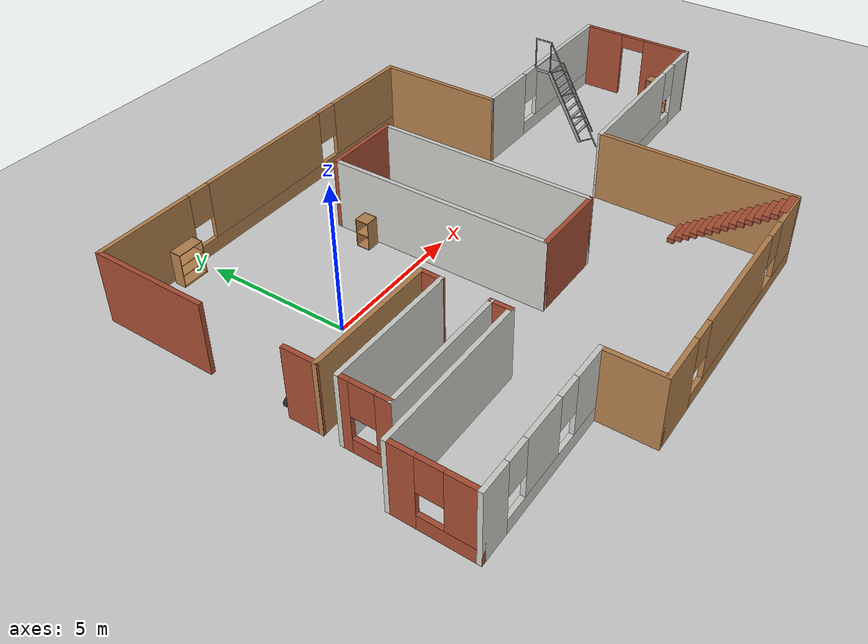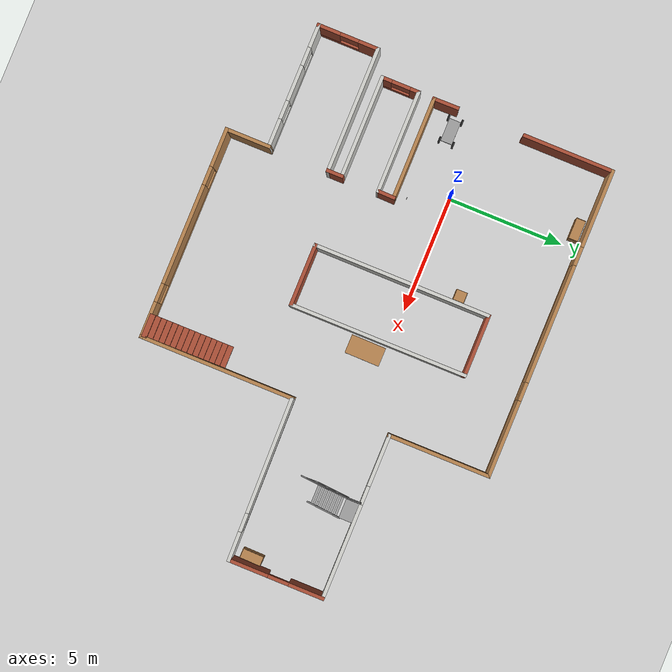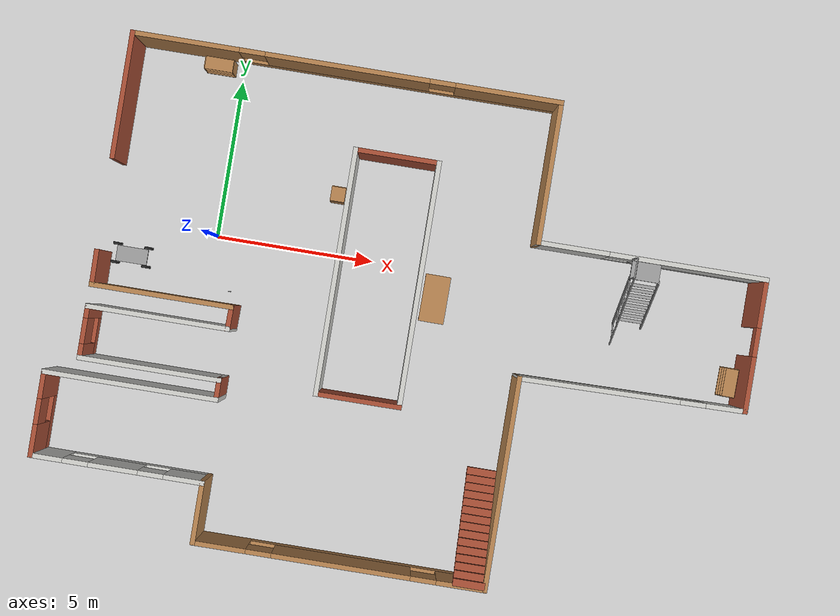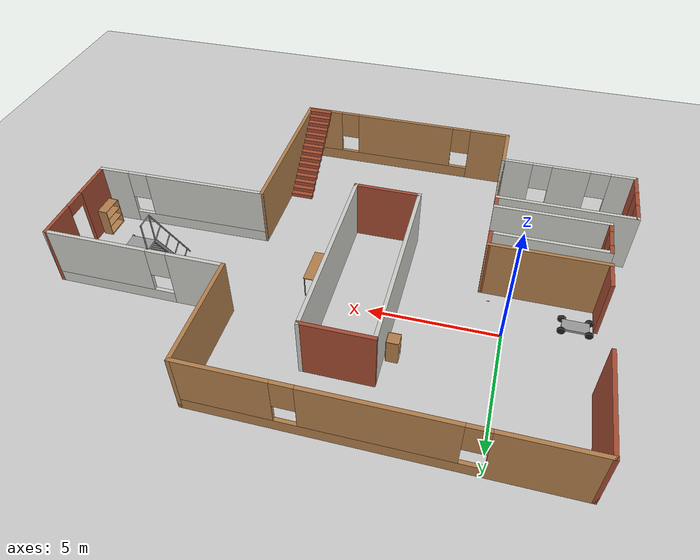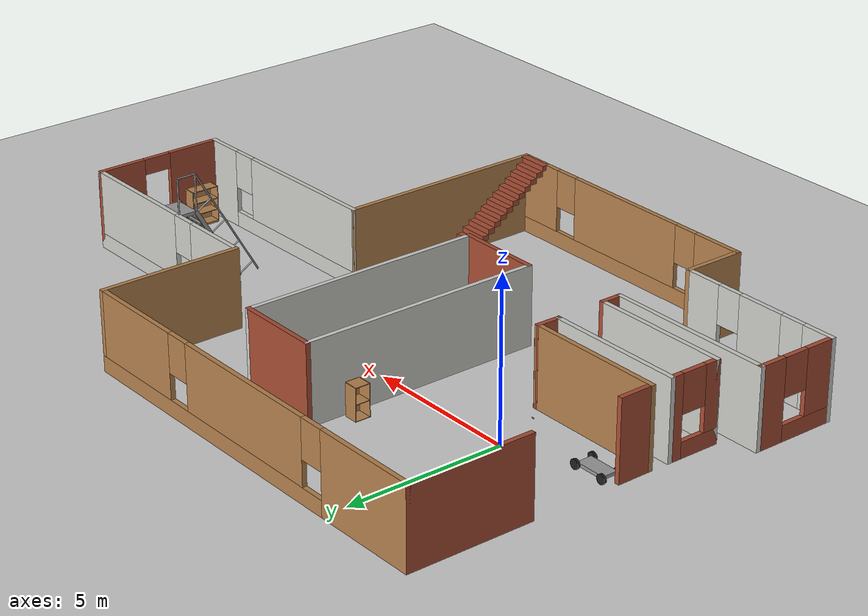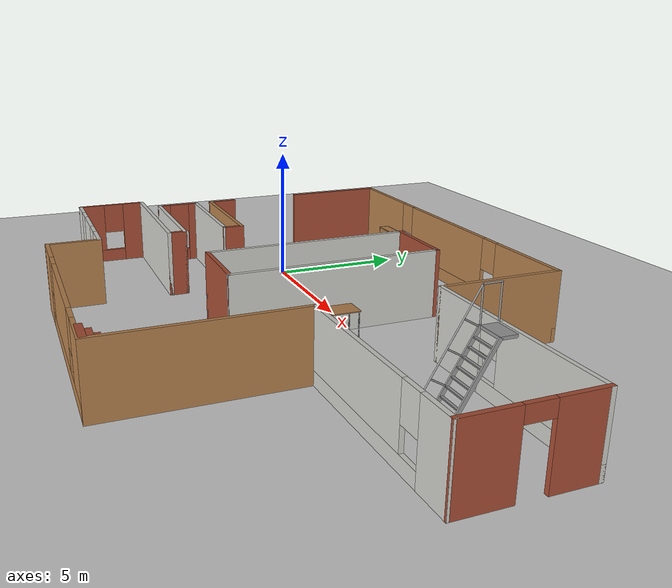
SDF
<sdf version="1.6">
 <world name="default">
  <light name="sun" type="directional">
   <pose>0 0 10 0 -0 0</pose>
   <diffuse>0.8 0.8 0.8 1</diffuse>
   <specular>0.2 0.2 0.2 1</specular>
   <attenuation>
    <range>1000</range>
    <constant>0.9</constant>
    <linear>0.01</linear>
    <quadratic>0.001</quadratic>
   </attenuation>
   <direction>-0.5 0.1 -0.9</direction>
  </light>
  <model name="ground_plane">
   <static>1</static>
   <link name="link">
    <collision name="collision">
     <geometry><plane><normal>0 0 1</normal><size>100 100</size></plane></geometry>
     <surface><friction><ode><mu>100</mu><mu2>50</mu2></ode></friction></surface>
    </collision>
    <visual name="visual">
     <cast_shadows>0</cast_shadows>
     <geometry><plane><normal>0 0 1</normal><size>100 100</size></plane></geometry>
     <material>
      <script><uri>file://media/materials/scripts/gazebo.material</uri><name>Gazebo/Grey</name></script>
     </material>
    </visual>
   </link>
  </model>
  <gravity>0 0 -9.8</gravity>
  <magnetic_field>6e-06 2.3e-05 -4.2e-05</magnetic_field>
  <atmosphere type="adiabatic"/>
  <physics name="default_physics" default="0" type="ode">
   <max_step_size>0.001</max_step_size>
   <real_time_factor>1</real_time_factor>
   <real_time_update_rate>1000</real_time_update_rate>
  </physics>
  <scene><ambient>0.4 0.4 0.4 1</ambient><background>0.7 0.7 0.7 1</background><shadows>1</shadows></scene>
  <spherical_coordinates>
   <surface_model>EARTH_WGS84</surface_model>
   <latitude_deg>0</latitude_deg>
   <longitude_deg>0</longitude_deg>
   <elevation>0</elevation>
   <heading_deg>0</heading_deg>
  </spherical_coordinates>
  <model name="my1">
   <pose>6.37403 -1.86892 0 0 -0 0</pose>
   <link name="Stairs_1">
    <visual name="Stairs_1_Visual_0">
     <pose>3.20471 -4.20963 0.083333 0 -0 0</pose>
     <geometry><box><size>1 0.233333 0.166667</size></box></geometry>
     <material>
      <script><uri>file://media/materials/scripts/gazebo.material</uri><name>Gazebo/Bricks</name></script>
      <ambient>1 1 1 1</ambient>
     </material>
     <meta><layer>0</layer></meta>
    </visual>
    <collision name="Stairs_1_Collision_0">
     <geometry><box><size>1 0.233333 0.166667</size></box></geometry>
     <pose>3.20471 -4.20963 0.083333 0 -0 0</pose>
    </collision>
    <visual name="Stairs_1_Visual_1">
     <pose>3.20471 -4.44296 0.25 0 -0 0</pose>
     <geometry><box><size>1 0.233333 0.166667</size></box></geometry>
     <material>
      <script><uri>file://media/materials/scripts/gazebo.material</uri><name>Gazebo/Bricks</name></script>
      <ambient>1 1 1 1</ambient>
     </material>
     <meta><layer>0</layer></meta>
    </visual>
    <collision name="Stairs_1_Collision_1">
     <geometry><box><size>1 0.233333 0.166667</size></box></geometry>
     <pose>3.20471 -4.44296 0.25 0 -0 0</pose>
    </collision>
    <visual name="Stairs_1_Visual_2">
     <pose>3.20471 -4.6763 0.416667 0 -0 0</pose>
     <geometry><box><size>1 0.233333 0.166667</size></box></geometry>
     <material>
      <script><uri>file://media/materials/scripts/gazebo.material</uri><name>Gazebo/Bricks</name></script>
      <ambient>1 1 1 1</ambient>
     </material>
     <meta><layer>0</layer></meta>
    </visual>
    <collision name="Stairs_1_Collision_2">
     <geometry><box><size>1 0.233333 0.166667</size></box></geometry>
     <pose>3.20471 -4.6763 0.416667 0 -0 0</pose>
    </collision>
    <visual name="Stairs_1_Visual_3">
     <pose>3.20471 -4.90963 0.583333 0 -0 0</pose>
     <geometry><box><size>1 0.233333 0.166667</size></box></geometry>
     <material>
      <script><uri>file://media/materials/scripts/gazebo.material</uri><name>Gazebo/Bricks</name></script>
      <ambient>1 1 1 1</ambient>
     </material>
     <meta><layer>0</layer></meta>
    </visual>
    <collision name="Stairs_1_Collision_3">
     <geometry><box><size>1 0.233333 0.166667</size></box></geometry>
     <pose>3.20471 -4.90963 0.583333 0 -0 0</pose>
    </collision>
    <visual name="Stairs_1_Visual_4">
     <pose>3.20471 -5.14296 0.75 0 -0 0</pose>
     <geometry><box><size>1 0.233333 0.166667</size></box></geometry>
     <material>
      <script><uri>file://media/materials/scripts/gazebo.material</uri><name>Gazebo/Bricks</name></script>
      <ambient>1 1 1 1</ambient>
     </material>
     <meta><layer>0</layer></meta>
    </visual>
    <collision name="Stairs_1_Collision_4">
     <geometry><box><size>1 0.233333 0.166667</size></box></geometry>
     <pose>3.20471 -5.14296 0.75 0 -0 0</pose>
    </collision>
    <visual name="Stairs_1_Visual_5">
     <pose>3.20471 -5.3763 0.916667 0 -0 0</pose>
     <geometry><box><size>1 0.233333 0.166667</size></box></geometry>
     <material>
      <script><uri>file://media/materials/scripts/gazebo.material</uri><name>Gazebo/Bricks</name></script>
      <ambient>1 1 1 1</ambient>
     </material>
     <meta><layer>0</layer></meta>
    </visual>
    <collision name="Stairs_1_Collision_5">
     <geometry><box><size>1 0.233333 0.166667</size></box></geometry>
     <pose>3.20471 -5.3763 0.916667 0 -0 0</pose>
    </collision>
    <visual name="Stairs_1_Visual_6">
     <pose>3.20471 -5.60963 1.08333 0 -0 0</pose>
     <geometry><box><size>1 0.233333 0.166667</size></box></geometry>
     <material>
      <script><uri>file://media/materials/scripts/gazebo.material</uri><name>Gazebo/Bricks</name></script>
      <ambient>1 1 1 1</ambient>
     </material>
     <meta><layer>0</layer></meta>
    </visual>
    <collision name="Stairs_1_Collision_6">
     <geometry><box><size>1 0.233333 0.166667</size></box></geometry>
     <pose>3.20471 -5.60963 1.08333 0 -0 0</pose>
    </collision>
    <visual name="Stairs_1_Visual_7">
     <pose>3.20471 -5.84296 1.25 0 -0 0</pose>
     <geometry><box><size>1 0.233333 0.166667</size></box></geometry>
     <material>
      <script><uri>file://media/materials/scripts/gazebo.material</uri><name>Gazebo/Bricks</name></script>
      <ambient>1 1 1 1</ambient>
     </material>
     <meta><layer>0</layer></meta>
    </visual>
    <collision name="Stairs_1_Collision_7">
     <geometry><box><size>1 0.233333 0.166667</size></box></geometry>
     <pose>3.20471 -5.84296 1.25 0 -0 0</pose>
    </collision>
    <visual name="Stairs_1_Visual_8">
     <pose>3.20471 -6.0763 1.41667 0 -0 0</pose>
     <geometry><box><size>1 0.233333 0.166667</size></box></geometry>
     <material>
      <script><uri>file://media/materials/scripts/gazebo.material</uri><name>Gazebo/Bricks</name></script>
      <ambient>1 1 1 1</ambient>
     </material>
     <meta><layer>0</layer></meta>
    </visual>
    <collision name="Stairs_1_Collision_8">
     <geometry><box><size>1 0.233333 0.166667</size></box></geometry>
     <pose>3.20471 -6.0763 1.41667 0 -0 0</pose>
    </collision>
    <visual name="Stairs_1_Visual_9">
     <pose>3.20471 -6.30963 1.58333 0 -0 0</pose>
     <geometry><box><size>1 0.233333 0.166667</size></box></geometry>
     <material>
      <script><uri>file://media/materials/scripts/gazebo.material</uri><name>Gazebo/Bricks</name></script>
      <ambient>1 1 1 1</ambient>
     </material>
     <meta><layer>0</layer></meta>
    </visual>
    <collision name="Stairs_1_Collision_9">
     <geometry><box><size>1 0.233333 0.166667</size></box></geometry>
     <pose>3.20471 -6.30963 1.58333 0 -0 0</pose>
    </collision>
    <visual name="Stairs_1_Visual_10">
     <pose>3.20471 -6.54296 1.75 0 -0 0</pose>
     <geometry><box><size>1 0.233333 0.166667</size></box></geometry>
     <material>
      <script><uri>file://media/materials/scripts/gazebo.material</uri><name>Gazebo/Bricks</name></script>
      <ambient>1 1 1 1</ambient>
     </material>
     <meta><layer>0</layer></meta>
    </visual>
    <collision name="Stairs_1_Collision_10">
     <geometry><box><size>1 0.233333 0.166667</size></box></geometry>
     <pose>3.20471 -6.54296 1.75 0 -0 0</pose>
    </collision>
    <visual name="Stairs_1_Visual_11">
     <pose>3.20471 -6.7763 1.91667 0 -0 0</pose>
     <geometry><box><size>1 0.233333 0.166667</size></box></geometry>
     <material>
      <script><uri>file://media/materials/scripts/gazebo.material</uri><name>Gazebo/Bricks</name></script>
      <ambient>1 1 1 1</ambient>
     </material>
     <meta><layer>0</layer></meta>
    </visual>
    <collision name="Stairs_1_Collision_11">
     <geometry><box><size>1 0.233333 0.166667</size></box></geometry>
     <pose>3.20471 -6.7763 1.91667 0 -0 0</pose>
    </collision>
    <visual name="Stairs_1_Visual_12">
     <pose>3.20471 -7.00963 2.08333 0 -0 0</pose>
     <geometry><box><size>1 0.233333 0.166667</size></box></geometry>
     <material>
      <script><uri>file://media/materials/scripts/gazebo.material</uri><name>Gazebo/Bricks</name></script>
      <ambient>1 1 1 1</ambient>
     </material>
     <meta><layer>0</layer></meta>
    </visual>
    <collision name="Stairs_1_Collision_12">
     <geometry><box><size>1 0.233333 0.166667</size></box></geometry>
     <pose>3.20471 -7.00963 2.08333 0 -0 0</pose>
    </collision>
    <visual name="Stairs_1_Visual_13">
     <pose>3.20471 -7.24296 2.25 0 -0 0</pose>
     <geometry><box><size>1 0.233333 0.166667</size></box></geometry>
     <material>
      <script><uri>file://media/materials/scripts/gazebo.material</uri><name>Gazebo/Bricks</name></script>
      <ambient>1 1 1 1</ambient>
     </material>
     <meta><layer>0</layer></meta>
    </visual>
    <collision name="Stairs_1_Collision_13">
     <geometry><box><size>1 0.233333 0.166667</size></box></geometry>
     <pose>3.20471 -7.24296 2.25 0 -0 0</pose>
    </collision>
    <visual name="Stairs_1_Visual_14">
     <pose>3.20471 -7.4763 2.41667 0 -0 0</pose>
     <geometry><box><size>1 0.233333 0.166667</size></box></geometry>
     <material>
      <script><uri>file://media/materials/scripts/gazebo.material</uri><name>Gazebo/Bricks</name></script>
      <ambient>1 1 1 1</ambient>
     </material>
     <meta><layer>0</layer></meta>
    </visual>
    <collision name="Stairs_1_Collision_14">
     <geometry><box><size>1 0.233333 0.166667</size></box></geometry>
     <pose>3.20471 -7.4763 2.41667 0 -0 0</pose>
    </collision>
   </link>
   <link name="Wall_13">
    <collision name="Wall_13_Collision">
     <geometry><box><size>4.5 0.15 2.5</size></box></geometry>
     <pose>0 0 1.25 0 -0 0</pose>
    </collision>
    <visual name="Wall_13_Visual">
     <pose>0 0 1.25 0 -0 0</pose>
     <geometry><box><size>4.5 0.15 2.5</size></box></geometry>
     <material>
      <script><uri>file://media/materials/scripts/gazebo.material</uri><name>Gazebo/Wood</name></script>
      <ambient>1 1 1 1</ambient>
     </material>
     <meta><layer>0</layer></meta>
    </visual>
    <pose>-7.54667 -0.254206 0 0 -0 3.14159</pose>
   </link>
   <link name="Wall_15">
    <collision name="Wall_15_Collision">
     <geometry><box><size>1.17118 0.15 2.5</size></box></geometry>
     <pose>0 0 1.25 0 -0 0</pose>
    </collision>
    <visual name="Wall_15_Visual">
     <pose>0 0 1.25 0 -0 0</pose>
     <geometry><box><size>1.17118 0.15 2.5</size></box></geometry>
     <material>
      <script><uri>file://media/materials/scripts/gazebo.material</uri><name>Gazebo/Bricks</name></script>
      <ambient>1 1 1 1</ambient>
     </material>
     <meta><layer>0</layer></meta>
    </visual>
    <pose>-9.72167 0.256343 0 0 -0 1.58367</pose>
   </link>
   <link name="Wall_18">
    <collision name="Wall_18_Collision">
     <geometry><box><size>0.829029 0.15 2.5</size></box></geometry>
     <pose>0 0 1.25 0 -0 0</pose>
    </collision>
    <visual name="Wall_18_Visual">
     <pose>0 0 1.25 0 -0 0</pose>
     <geometry><box><size>0.829029 0.15 2.5</size></box></geometry>
     <material>
      <script><uri>file://media/materials/scripts/gazebo.material</uri><name>Gazebo/Bricks</name></script>
      <ambient>1 1 1 1</ambient>
     </material>
     <meta><layer>0</layer></meta>
    </visual>
    <pose>-5.37167 -0.593657 0 0 0 -1.59016</pose>
   </link>
   <link name="Wall_19">
    <collision name="Wall_19_Collision">
     <geometry><box><size>4.5 0.15 2.5</size></box></geometry>
     <pose>0 0 1.25 0 -0 0</pose>
    </collision>
    <visual name="Wall_19_Visual">
     <pose>0 0 1.25 0 -0 0</pose>
     <geometry><box><size>4.5 0.15 2.5</size></box></geometry>
     <material>
      <script><uri>file://media/materials/scripts/gazebo.material</uri><name>Gazebo/CeilingTiled</name></script>
      <ambient>1 1 1 1</ambient>
     </material>
     <meta><layer>0</layer></meta>
    </visual>
    <pose>-7.55325 -0.933108 0 0 -0 3.14159</pose>
   </link>
   <link name="Wall_20">
    <pose>-9.72825 -1.73311 0 0 0 -1.5708</pose>
    <visual name="Wall_20_Visual_0">
     <pose>-0.654101 0 1.25 0 -0 0</pose>
     <geometry><box><size>0.441799 0.15 2.5</size></box></geometry>
     <material>
      <script><uri>file://media/materials/scripts/gazebo.material</uri><name>Gazebo/Bricks</name></script>
      <ambient>1 1 1 1</ambient>
     </material>
     <meta><layer>0</layer></meta>
    </visual>
    <collision name="Wall_20_Collision_0">
     <geometry><box><size>0.441799 0.15 2.5</size></box></geometry>
     <pose>-0.654101 0 1.25 0 -0 0</pose>
    </collision>
    <visual name="Wall_20_Visual_1">
     <pose>0.220899 0 0.25 0 -0 0</pose>
     <geometry><box><size>1.3082 0.15 0.5</size></box></geometry>
     <material>
      <script><uri>file://media/materials/scripts/gazebo.material</uri><name>Gazebo/Bricks</name></script>
      <ambient>1 1 1 1</ambient>
     </material>
     <meta><layer>0</layer></meta>
    </visual>
    <collision name="Wall_20_Collision_1">
     <geometry><box><size>1.3082 0.15 0.5</size></box></geometry>
     <pose>0.220899 0 0.25 0 -0 0</pose>
    </collision>
    <visual name="Wall_20_Visual_2">
     <pose>0.620899 0 1.5 0 -0 0</pose>
     <geometry><box><size>0.508201 0.15 2</size></box></geometry>
     <material>
      <script><uri>file://media/materials/scripts/gazebo.material</uri><name>Gazebo/Bricks</name></script>
      <ambient>1 1 1 1</ambient>
     </material>
     <meta><layer>0</layer></meta>
    </visual>
    <collision name="Wall_20_Collision_2">
     <geometry><box><size>0.508201 0.15 2</size></box></geometry>
     <pose>0.620899 0 1.5 0 -0 0</pose>
    </collision>
    <visual name="Wall_20_Visual_3">
     <pose>-0.033201 0 1.9 0 -0 0</pose>
     <geometry><box><size>0.8 0.15 1.2</size></box></geometry>
     <material>
      <script><uri>file://media/materials/scripts/gazebo.material</uri><name>Gazebo/Bricks</name></script>
      <ambient>1 1 1 1</ambient>
     </material>
     <meta><layer>0</layer></meta>
    </visual>
    <collision name="Wall_20_Collision_3">
     <geometry><box><size>0.8 0.15 1.2</size></box></geometry>
     <pose>-0.033201 0 1.9 0 -0 0</pose>
    </collision>
   </link>
   <link name="Wall_21">
    <collision name="Wall_21_Collision">
     <geometry><box><size>4.5 0.15 2.5</size></box></geometry>
     <pose>0 0 1.25 0 -0 0</pose>
    </collision>
    <visual name="Wall_21_Visual">
     <pose>0 0 1.25 0 -0 0</pose>
     <geometry><box><size>4.5 0.15 2.5</size></box></geometry>
     <material>
      <script><uri>file://media/materials/scripts/gazebo.material</uri><name>Gazebo/CeilingTiled</name></script>
      <ambient>1 1 1 1</ambient>
     </material>
     <meta><layer>0</layer></meta>
    </visual>
    <pose>-7.55325 -2.53311 0 0 -0 0</pose>
   </link>
   <link name="Wall_24">
    <collision name="Wall_24_Collision">
     <geometry><box><size>0.75 0.15 2.5</size></box></geometry>
     <pose>0 0 1.25 0 -0 0</pose>
    </collision>
    <visual name="Wall_24_Visual">
     <pose>0 0 1.25 0 -0 0</pose>
     <geometry><box><size>0.75 0.15 2.5</size></box></geometry>
     <material>
      <script><uri>file://media/materials/scripts/gazebo.material</uri><name>Gazebo/Bricks</name></script>
      <ambient>1 1 1 1</ambient>
     </material>
     <meta><layer>0</layer></meta>
    </visual>
    <pose>-5.37825 -2.83311 0 0 0 -1.5708</pose>
   </link>
   <link name="Wall_25">
    <collision name="Wall_25_Collision">
     <geometry><box><size>5.5 0.15 2.5</size></box></geometry>
     <pose>0 0 1.25 0 -0 0</pose>
    </collision>
    <visual name="Wall_25_Visual">
     <pose>0 0 1.25 0 -0 0</pose>
     <geometry><box><size>5.5 0.15 2.5</size></box></geometry>
     <material>
      <script><uri>file://media/materials/scripts/gazebo.material</uri><name>Gazebo/CeilingTiled</name></script>
      <ambient>1 1 1 1</ambient>
     </material>
     <meta><layer>0</layer></meta>
    </visual>
    <pose>-8.05325 -3.13311 0 0 -0 3.14159</pose>
   </link>
   <link name="Wall_26">
    <pose>-10.7282 -4.43311 0 0 0 -1.5708</pose>
    <visual name="Wall_26_Visual_0">
     <pose>-0.917525 0 1.25 0 -0 0</pose>
     <geometry><box><size>0.914949 0.15 2.5</size></box></geometry>
     <material>
      <script><uri>file://media/materials/scripts/gazebo.material</uri><name>Gazebo/Bricks</name></script>
      <ambient>1 1 1 1</ambient>
     </material>
     <meta><layer>0</layer></meta>
    </visual>
    <collision name="Wall_26_Collision_0">
     <geometry><box><size>0.914949 0.15 2.5</size></box></geometry>
     <pose>-0.917525 0 1.25 0 -0 0</pose>
    </collision>
    <visual name="Wall_26_Visual_1">
     <pose>0.457475 0 0.25 0 -0 0</pose>
     <geometry><box><size>1.83505 0.15 0.5</size></box></geometry>
     <material>
      <script><uri>file://media/materials/scripts/gazebo.material</uri><name>Gazebo/Bricks</name></script>
      <ambient>1 1 1 1</ambient>
     </material>
     <meta><layer>0</layer></meta>
    </visual>
    <collision name="Wall_26_Collision_1">
     <geometry><box><size>1.83505 0.15 0.5</size></box></geometry>
     <pose>0.457475 0 0.25 0 -0 0</pose>
    </collision>
    <visual name="Wall_26_Visual_2">
     <pose>0.857475 0 1.5 0 -0 0</pose>
     <geometry><box><size>1.03505 0.15 2</size></box></geometry>
     <material>
      <script><uri>file://media/materials/scripts/gazebo.material</uri><name>Gazebo/Bricks</name></script>
      <ambient>1 1 1 1</ambient>
     </material>
     <meta><layer>0</layer></meta>
    </visual>
    <collision name="Wall_26_Collision_2">
     <geometry><box><size>1.03505 0.15 2</size></box></geometry>
     <pose>0.857475 0 1.5 0 -0 0</pose>
    </collision>
    <visual name="Wall_26_Visual_3">
     <pose>-0.060051 0 1.9 0 -0 0</pose>
     <geometry><box><size>0.8 0.15 1.2</size></box></geometry>
     <material>
      <script><uri>file://media/materials/scripts/gazebo.material</uri><name>Gazebo/Bricks</name></script>
      <ambient>1 1 1 1</ambient>
     </material>
     <meta><layer>0</layer></meta>
    </visual>
    <collision name="Wall_26_Collision_3">
     <geometry><box><size>0.8 0.15 1.2</size></box></geometry>
     <pose>-0.060051 0 1.9 0 -0 0</pose>
    </collision>
   </link>
   <link name="Wall_27">
    <pose>-8.05325 -5.73311 0 0 -0 0</pose>
    <visual name="Wall_27_Visual_0">
     <pose>-2.22077 0 1.25 0 -0 0</pose>
     <geometry><box><size>1.05847 0.15 2.5</size></box></geometry>
     <material>
      <script><uri>file://media/materials/scripts/gazebo.material</uri><name>Gazebo/CeilingTiled</name></script>
      <ambient>1 1 1 1</ambient>
     </material>
     <meta><layer>0</layer></meta>
    </visual>
    <collision name="Wall_27_Collision_0">
     <geometry><box><size>1.05847 0.15 2.5</size></box></geometry>
     <pose>-2.22077 0 1.25 0 -0 0</pose>
    </collision>
    <visual name="Wall_27_Visual_1">
     <pose>0.529234 0 0.25 0 -0 0</pose>
     <geometry><box><size>4.44153 0.15 0.5</size></box></geometry>
     <material>
      <script><uri>file://media/materials/scripts/gazebo.material</uri><name>Gazebo/CeilingTiled</name></script>
      <ambient>1 1 1 1</ambient>
     </material>
     <meta><layer>0</layer></meta>
    </visual>
    <collision name="Wall_27_Collision_1">
     <geometry><box><size>4.44153 0.15 0.5</size></box></geometry>
     <pose>0.529234 0 0.25 0 -0 0</pose>
    </collision>
    <visual name="Wall_27_Visual_2">
     <pose>-0.116533 0 1.5 0 -0 0</pose>
     <geometry><box><size>1.55 0.15 2</size></box></geometry>
     <material>
      <script><uri>file://media/materials/scripts/gazebo.material</uri><name>Gazebo/CeilingTiled</name></script>
      <ambient>1 1 1 1</ambient>
     </material>
     <meta><layer>0</layer></meta>
    </visual>
    <collision name="Wall_27_Collision_2">
     <geometry><box><size>1.55 0.15 2</size></box></geometry>
     <pose>-0.116533 0 1.5 0 -0 0</pose>
    </collision>
    <visual name="Wall_27_Visual_3">
     <pose>2.10423 0 1.5 0 -0 0</pose>
     <geometry><box><size>1.29153 0.15 2</size></box></geometry>
     <material>
      <script><uri>file://media/materials/scripts/gazebo.material</uri><name>Gazebo/CeilingTiled</name></script>
      <ambient>1 1 1 1</ambient>
     </material>
     <meta><layer>0</layer></meta>
    </visual>
    <collision name="Wall_27_Collision_3">
     <geometry><box><size>1.29153 0.15 2</size></box></geometry>
     <pose>2.10423 0 1.5 0 -0 0</pose>
    </collision>
    <visual name="Wall_27_Visual_4">
     <pose>-1.29153 0 1.9 0 -0 0</pose>
     <geometry><box><size>0.8 0.15 1.2</size></box></geometry>
     <material>
      <script><uri>file://media/materials/scripts/gazebo.material</uri><name>Gazebo/CeilingTiled</name></script>
      <ambient>1 1 1 1</ambient>
     </material>
     <meta><layer>0</layer></meta>
    </visual>
    <collision name="Wall_27_Collision_4">
     <geometry><box><size>0.8 0.15 1.2</size></box></geometry>
     <pose>-1.29153 0 1.9 0 -0 0</pose>
    </collision>
    <visual name="Wall_27_Visual_5">
     <pose>1.05847 0 1.9 0 -0 0</pose>
     <geometry><box><size>0.8 0.15 1.2</size></box></geometry>
     <material>
      <script><uri>file://media/materials/scripts/gazebo.material</uri><name>Gazebo/CeilingTiled</name></script>
      <ambient>1 1 1 1</ambient>
     </material>
     <meta><layer>0</layer></meta>
    </visual>
    <collision name="Wall_27_Collision_5">
     <geometry><box><size>0.8 0.15 1.2</size></box></geometry>
     <pose>1.05847 0 1.9 0 -0 0</pose>
    </collision>
   </link>
   <link name="Wall_30">
    <collision name="Wall_30_Collision">
     <geometry><box><size>2 0.15 2.5</size></box></geometry>
     <pose>0 0 1.25 0 -0 0</pose>
    </collision>
    <visual name="Wall_30_Visual">
     <pose>0 0 1.25 0 -0 0</pose>
     <geometry><box><size>2 0.15 2.5</size></box></geometry>
     <material>
      <script><uri>file://media/materials/scripts/gazebo.material</uri><name>Gazebo/Wood</name></script>
      <ambient>1 1 1 1</ambient>
     </material>
     <meta><layer>0</layer></meta>
    </visual>
    <pose>-5.37825 -6.65811 0 0 0 -1.5708</pose>
   </link>
   <link name="Wall_31">
    <pose>-0.828247 -7.58311 0 0 -0 0</pose>
    <visual name="Wall_31_Visual_0">
     <pose>-3.76785 0 1.25 0 -0 0</pose>
     <geometry><box><size>1.71431 0.15 2.5</size></box></geometry>
     <material>
      <script><uri>file://media/materials/scripts/gazebo.material</uri><name>Gazebo/Wood</name></script>
      <ambient>1 1 1 1</ambient>
     </material>
     <meta><layer>0</layer></meta>
    </visual>
    <collision name="Wall_31_Collision_0">
     <geometry><box><size>1.71431 0.15 2.5</size></box></geometry>
     <pose>-3.76785 0 1.25 0 -0 0</pose>
    </collision>
    <visual name="Wall_31_Visual_1">
     <pose>0.857154 0 0.25 0 -0 0</pose>
     <geometry><box><size>7.53569 0.15 0.5</size></box></geometry>
     <material>
      <script><uri>file://media/materials/scripts/gazebo.material</uri><name>Gazebo/Wood</name></script>
      <ambient>1 1 1 1</ambient>
     </material>
     <meta><layer>0</layer></meta>
    </visual>
    <collision name="Wall_31_Collision_1">
     <geometry><box><size>7.53569 0.15 0.5</size></box></geometry>
     <pose>0.857154 0 0.25 0 -0 0</pose>
    </collision>
    <visual name="Wall_31_Visual_2">
     <pose>0.056227 0 1.5 0 -0 0</pose>
     <geometry><box><size>4.33384 0.15 2</size></box></geometry>
     <material>
      <script><uri>file://media/materials/scripts/gazebo.material</uri><name>Gazebo/Wood</name></script>
      <ambient>1 1 1 1</ambient>
     </material>
     <meta><layer>0</layer></meta>
    </visual>
    <collision name="Wall_31_Collision_2">
     <geometry><box><size>4.33384 0.15 2</size></box></geometry>
     <pose>0.056227 0 1.5 0 -0 0</pose>
    </collision>
    <visual name="Wall_31_Visual_3">
     <pose>3.82407 0 1.5 0 -0 0</pose>
     <geometry><box><size>1.60185 0.15 2</size></box></geometry>
     <material>
      <script><uri>file://media/materials/scripts/gazebo.material</uri><name>Gazebo/Wood</name></script>
      <ambient>1 1 1 1</ambient>
     </material>
     <meta><layer>0</layer></meta>
    </visual>
    <collision name="Wall_31_Collision_3">
     <geometry><box><size>1.60185 0.15 2</size></box></geometry>
     <pose>3.82407 0 1.5 0 -0 0</pose>
    </collision>
    <visual name="Wall_31_Visual_4">
     <pose>-2.51069 0 1.9 0 -0 0</pose>
     <geometry><box><size>0.8 0.15 1.2</size></box></geometry>
     <material>
      <script><uri>file://media/materials/scripts/gazebo.material</uri><name>Gazebo/Wood</name></script>
      <ambient>1 1 1 1</ambient>
     </material>
     <meta><layer>0</layer></meta>
    </visual>
    <collision name="Wall_31_Collision_4">
     <geometry><box><size>0.8 0.15 1.2</size></box></geometry>
     <pose>-2.51069 0 1.9 0 -0 0</pose>
    </collision>
    <visual name="Wall_31_Visual_5">
     <pose>2.62315 0 1.9 0 -0 0</pose>
     <geometry><box><size>0.8 0.15 1.2</size></box></geometry>
     <material>
      <script><uri>file://media/materials/scripts/gazebo.material</uri><name>Gazebo/Wood</name></script>
      <ambient>1 1 1 1</ambient>
     </material>
     <meta><layer>0</layer></meta>
    </visual>
    <collision name="Wall_31_Collision_5">
     <geometry><box><size>0.8 0.15 1.2</size></box></geometry>
     <pose>2.62315 0 1.9 0 -0 0</pose>
    </collision>
   </link>
   <link name="Wall_32">
    <collision name="Wall_32_Collision">
     <geometry><box><size>6.75 0.15 2.5</size></box></geometry>
     <pose>0 0 1.25 0 -0 0</pose>
    </collision>
    <visual name="Wall_32_Visual">
     <pose>0 0 1.25 0 -0 0</pose>
     <geometry><box><size>6.75 0.15 2.5</size></box></geometry>
     <material>
      <script><uri>file://media/materials/scripts/gazebo.material</uri><name>Gazebo/Wood</name></script>
      <ambient>1 1 1 1</ambient>
     </material>
     <meta><layer>0</layer></meta>
    </visual>
    <pose>3.72175 -4.28311 0 0 -0 1.5708</pose>
   </link>
   <link name="Wall_34">
    <collision name="Wall_34_Collision">
     <geometry><box><size>4 0.15 2.5</size></box></geometry>
     <pose>0 0 1.25 0 -0 0</pose>
    </collision>
    <visual name="Wall_34_Visual">
     <pose>0 0 1.25 0 -0 0</pose>
     <geometry><box><size>4 0.15 2.5</size></box></geometry>
     <material>
      <script><uri>file://media/materials/scripts/gazebo.material</uri><name>Gazebo/Bricks</name></script>
      <ambient>1 1 1 1</ambient>
     </material>
     <meta><layer>0</layer></meta>
    </visual>
    <pose>-9.72299 5.65811 0 0 -0 1.5708</pose>
   </link>
   <link name="Wall_35">
    <pose>-3.04799 7.58311 0 0 -0 0</pose>
    <visual name="Wall_35_Visual_0">
     <pose>-5.05049 0 1.25 0 -0 0</pose>
     <geometry><box><size>3.39903 0.15 2.5</size></box></geometry>
     <material>
      <script><uri>file://media/materials/scripts/gazebo.material</uri><name>Gazebo/Wood</name></script>
      <ambient>1 1 1 1</ambient>
     </material>
     <meta><layer>0</layer></meta>
    </visual>
    <collision name="Wall_35_Collision_0">
     <geometry><box><size>3.39903 0.15 2.5</size></box></geometry>
     <pose>-5.05049 0 1.25 0 -0 0</pose>
    </collision>
    <visual name="Wall_35_Visual_1">
     <pose>1.69951 0 0.25 0 -0 0</pose>
     <geometry><box><size>10.101 0.15 0.5</size></box></geometry>
     <material>
      <script><uri>file://media/materials/scripts/gazebo.material</uri><name>Gazebo/Wood</name></script>
      <ambient>1 1 1 1</ambient>
     </material>
     <meta><layer>0</layer></meta>
    </visual>
    <collision name="Wall_35_Collision_1">
     <geometry><box><size>10.101 0.15 0.5</size></box></geometry>
     <pose>1.69951 0 0.25 0 -0 0</pose>
    </collision>
    <visual name="Wall_35_Visual_2">
     <pose>0.01495 0 1.5 0 -0 0</pose>
     <geometry><box><size>5.13185 0.15 2</size></box></geometry>
     <material>
      <script><uri>file://media/materials/scripts/gazebo.material</uri><name>Gazebo/Wood</name></script>
      <ambient>1 1 1 1</ambient>
     </material>
     <meta><layer>0</layer></meta>
    </visual>
    <collision name="Wall_35_Collision_2">
     <geometry><box><size>5.13185 0.15 2</size></box></geometry>
     <pose>0.01495 0 1.5 0 -0 0</pose>
    </collision>
    <visual name="Wall_35_Visual_3">
     <pose>5.06544 0 1.5 0 -0 0</pose>
     <geometry><box><size>3.36913 0.15 2</size></box></geometry>
     <material>
      <script><uri>file://media/materials/scripts/gazebo.material</uri><name>Gazebo/Wood</name></script>
      <ambient>1 1 1 1</ambient>
     </material>
     <meta><layer>0</layer></meta>
    </visual>
    <collision name="Wall_35_Collision_3">
     <geometry><box><size>3.36913 0.15 2</size></box></geometry>
     <pose>5.06544 0 1.5 0 -0 0</pose>
    </collision>
    <visual name="Wall_35_Visual_4">
     <pose>-2.95097 0 1.9 0 -0 0</pose>
     <geometry><box><size>0.8 0.15 1.2</size></box></geometry>
     <material>
      <script><uri>file://media/materials/scripts/gazebo.material</uri><name>Gazebo/Wood</name></script>
      <ambient>1 1 1 1</ambient>
     </material>
     <meta><layer>0</layer></meta>
    </visual>
    <collision name="Wall_35_Collision_4">
     <geometry><box><size>0.8 0.15 1.2</size></box></geometry>
     <pose>-2.95097 0 1.9 0 -0 0</pose>
    </collision>
    <visual name="Wall_35_Visual_5">
     <pose>2.98087 0 1.9 0 -0 0</pose>
     <geometry><box><size>0.8 0.15 1.2</size></box></geometry>
     <material>
      <script><uri>file://media/materials/scripts/gazebo.material</uri><name>Gazebo/Wood</name></script>
      <ambient>1 1 1 1</ambient>
     </material>
     <meta><layer>0</layer></meta>
    </visual>
    <collision name="Wall_35_Collision_5">
     <geometry><box><size>0.8 0.15 1.2</size></box></geometry>
     <pose>2.98087 0 1.9 0 -0 0</pose>
    </collision>
   </link>
   <link name="Wall_36">
    <collision name="Wall_36_Collision">
     <geometry><box><size>4.5 0.15 2.5</size></box></geometry>
     <pose>0 0 1.25 0 -0 0</pose>
    </collision>
    <visual name="Wall_36_Visual">
     <pose>0 0 1.25 0 -0 0</pose>
     <geometry><box><size>4.5 0.15 2.5</size></box></geometry>
     <material>
      <script><uri>file://media/materials/scripts/gazebo.material</uri><name>Gazebo/Wood</name></script>
      <ambient>1 1 1 1</ambient>
     </material>
     <meta><layer>0</layer></meta>
    </visual>
    <pose>3.62701 5.40811 0 0 0 -1.5708</pose>
   </link>
   <link name="Wall_37">
    <pose>7.17701 3.23311 0 0 -0 0</pose>
    <visual name="Wall_37_Visual_0">
     <pose>-2.48244 0 1.25 0 -0 0</pose>
     <geometry><box><size>2.28512 0.15 2.5</size></box></geometry>
     <material>
      <script><uri>file://media/materials/scripts/gazebo.material</uri><name>Gazebo/CeilingTiled</name></script>
      <ambient>1 1 1 1</ambient>
     </material>
     <meta><layer>0</layer></meta>
    </visual>
    <collision name="Wall_37_Collision_0">
     <geometry><box><size>2.28512 0.15 2.5</size></box></geometry>
     <pose>-2.48244 0 1.25 0 -0 0</pose>
    </collision>
    <visual name="Wall_37_Visual_1">
     <pose>1.14256 0 0.25 0 -0 0</pose>
     <geometry><box><size>4.96488 0.15 0.5</size></box></geometry>
     <material>
      <script><uri>file://media/materials/scripts/gazebo.material</uri><name>Gazebo/CeilingTiled</name></script>
      <ambient>1 1 1 1</ambient>
     </material>
     <meta><layer>0</layer></meta>
    </visual>
    <collision name="Wall_37_Collision_1">
     <geometry><box><size>4.96488 0.15 0.5</size></box></geometry>
     <pose>1.14256 0 0.25 0 -0 0</pose>
    </collision>
    <visual name="Wall_37_Visual_2">
     <pose>1.54256 0 1.5 0 -0 0</pose>
     <geometry><box><size>4.16488 0.15 2</size></box></geometry>
     <material>
      <script><uri>file://media/materials/scripts/gazebo.material</uri><name>Gazebo/CeilingTiled</name></script>
      <ambient>1 1 1 1</ambient>
     </material>
     <meta><layer>0</layer></meta>
    </visual>
    <collision name="Wall_37_Collision_2">
     <geometry><box><size>4.16488 0.15 2</size></box></geometry>
     <pose>1.54256 0 1.5 0 -0 0</pose>
    </collision>
    <visual name="Wall_37_Visual_3">
     <pose>-0.93988 0 1.9 0 -0 0</pose>
     <geometry><box><size>0.8 0.15 1.2</size></box></geometry>
     <material>
      <script><uri>file://media/materials/scripts/gazebo.material</uri><name>Gazebo/CeilingTiled</name></script>
      <ambient>1 1 1 1</ambient>
     </material>
     <meta><layer>0</layer></meta>
    </visual>
    <collision name="Wall_37_Collision_3">
     <geometry><box><size>0.8 0.15 1.2</size></box></geometry>
     <pose>-0.93988 0 1.9 0 -0 0</pose>
    </collision>
   </link>
   <link name="Wall_38">
    <pose>10.727 1.18311 0 0 0 -1.5708</pose>
    <visual name="Wall_38_Visual_0">
     <pose>-1.33889 0 1.25 0 -0 0</pose>
     <geometry><box><size>1.57222 0.15 2.5</size></box></geometry>
     <material>
      <script><uri>file://media/materials/scripts/gazebo.material</uri><name>Gazebo/Bricks</name></script>
      <ambient>1 1 1 1</ambient>
     </material>
     <meta><layer>0</layer></meta>
    </visual>
    <collision name="Wall_38_Collision_0">
     <geometry><box><size>1.57222 0.15 2.5</size></box></geometry>
     <pose>-1.33889 0 1.25 0 -0 0</pose>
    </collision>
    <visual name="Wall_38_Visual_1">
     <pose>1.23611 0 1.25 0 -0 0</pose>
     <geometry><box><size>1.77778 0.15 2.5</size></box></geometry>
     <material>
      <script><uri>file://media/materials/scripts/gazebo.material</uri><name>Gazebo/Bricks</name></script>
      <ambient>1 1 1 1</ambient>
     </material>
     <meta><layer>0</layer></meta>
    </visual>
    <collision name="Wall_38_Collision_1">
     <geometry><box><size>1.77778 0.15 2.5</size></box></geometry>
     <pose>1.23611 0 1.25 0 -0 0</pose>
    </collision>
    <visual name="Wall_38_Visual_2">
     <pose>-0.102782 0 2.25 0 -0 0</pose>
     <geometry><box><size>0.9 0.15 0.5</size></box></geometry>
     <material>
      <script><uri>file://media/materials/scripts/gazebo.material</uri><name>Gazebo/Bricks</name></script>
      <ambient>1 1 1 1</ambient>
     </material>
     <meta><layer>0</layer></meta>
    </visual>
    <collision name="Wall_38_Collision_2">
     <geometry><box><size>0.9 0.15 0.5</size></box></geometry>
     <pose>-0.102782 0 2.25 0 -0 0</pose>
    </collision>
   </link>
   <link name="Wall_39">
    <pose>7.22438 -0.925 0 0 0 -3.125</pose>
    <visual name="Wall_39_Visual_0">
     <pose>-2.9313 0 1.25 0 -0 0</pose>
     <geometry><box><size>1.29363 0.15 2.5</size></box></geometry>
     <material>
      <script><uri>file://media/materials/scripts/gazebo.material</uri><name>Gazebo/CeilingTiled</name></script>
      <ambient>1 1 1 1</ambient>
     </material>
     <meta><layer>0</layer></meta>
    </visual>
    <collision name="Wall_39_Collision_0">
     <geometry><box><size>1.29363 0.15 2.5</size></box></geometry>
     <pose>-2.9313 0 1.25 0 -0 0</pose>
    </collision>
    <visual name="Wall_39_Visual_1">
     <pose>0.646816 0 0.25 0 -0 0</pose>
     <geometry><box><size>5.86259 0.15 0.5</size></box></geometry>
     <material>
      <script><uri>file://media/materials/scripts/gazebo.material</uri><name>Gazebo/CeilingTiled</name></script>
      <ambient>1 1 1 1</ambient>
     </material>
     <meta><layer>0</layer></meta>
    </visual>
    <collision name="Wall_39_Collision_1">
     <geometry><box><size>5.86259 0.15 0.5</size></box></geometry>
     <pose>0.646816 0 0.25 0 -0 0</pose>
    </collision>
    <visual name="Wall_39_Visual_2">
     <pose>1.04682 0 1.5 0 -0 0</pose>
     <geometry><box><size>5.06259 0.15 2</size></box></geometry>
     <material>
      <script><uri>file://media/materials/scripts/gazebo.material</uri><name>Gazebo/CeilingTiled</name></script>
      <ambient>1 1 1 1</ambient>
     </material>
     <meta><layer>0</layer></meta>
    </visual>
    <collision name="Wall_39_Collision_2">
     <geometry><box><size>5.06259 0.15 2</size></box></geometry>
     <pose>1.04682 0 1.5 0 -0 0</pose>
    </collision>
    <visual name="Wall_39_Visual_3">
     <pose>-1.88448 0 1.9 0 -0 0</pose>
     <geometry><box><size>0.8 0.15 1.2</size></box></geometry>
     <material>
      <script><uri>file://media/materials/scripts/gazebo.material</uri><name>Gazebo/CeilingTiled</name></script>
      <ambient>1 1 1 1</ambient>
     </material>
     <meta><layer>0</layer></meta>
    </visual>
    <collision name="Wall_39_Collision_3">
     <geometry><box><size>0.8 0.15 1.2</size></box></geometry>
     <pose>-1.88448 0 1.9 0 -0 0</pose>
    </collision>
   </link>
   <link name="Wall_41">
    <collision name="Wall_41_Collision">
     <geometry><box><size>7.75 0.15 2.5</size></box></geometry>
     <pose>0 0 1.25 0 -0 0</pose>
    </collision>
    <visual name="Wall_41_Visual">
     <pose>0 0 1.25 0 -0 0</pose>
     <geometry><box><size>7.75 0.15 2.5</size></box></geometry>
     <material>
      <script><uri>file://media/materials/scripts/gazebo.material</uri><name>Gazebo/CeilingTiled</name></script>
      <ambient>1 1 1 1</ambient>
     </material>
     <meta><layer>0</layer></meta>
    </visual>
    <pose>-2.38133 1.34292 0 0 0 -1.5708</pose>
   </link>
   <link name="Wall_42">
    <collision name="Wall_42_Collision">
     <geometry><box><size>2.75 0.15 2.5</size></box></geometry>
     <pose>0 0 1.25 0 -0 0</pose>
    </collision>
    <visual name="Wall_42_Visual">
     <pose>0 0 1.25 0 -0 0</pose>
     <geometry><box><size>2.75 0.15 2.5</size></box></geometry>
     <material>
      <script><uri>file://media/materials/scripts/gazebo.material</uri><name>Gazebo/Bricks</name></script>
      <ambient>1 1 1 1</ambient>
     </material>
     <meta><layer>0</layer></meta>
    </visual>
    <pose>-1.08133 -2.45708 0 0 -0 0</pose>
   </link>
   <link name="Wall_43">
    <collision name="Wall_43_Collision">
     <geometry><box><size>7.75 0.15 2.5</size></box></geometry>
     <pose>0 0 1.25 0 -0 0</pose>
    </collision>
    <visual name="Wall_43_Visual">
     <pose>0 0 1.25 0 -0 0</pose>
     <geometry><box><size>7.75 0.15 2.5</size></box></geometry>
     <material>
      <script><uri>file://media/materials/scripts/gazebo.material</uri><name>Gazebo/CeilingTiled</name></script>
      <ambient>1 1 1 1</ambient>
     </material>
     <meta><layer>0</layer></meta>
    </visual>
    <pose>0.218668 1.34292 0 0 -0 1.5708</pose>
   </link>
   <link name="Wall_44">
    <collision name="Wall_44_Collision">
     <geometry><box><size>2.75 0.15 2.5</size></box></geometry>
     <pose>0 0 1.25 0 -0 0</pose>
    </collision>
    <visual name="Wall_44_Visual">
     <pose>0 0 1.25 0 -0 0</pose>
     <geometry><box><size>2.75 0.15 2.5</size></box></geometry>
     <material>
      <script><uri>file://media/materials/scripts/gazebo.material</uri><name>Gazebo/Bricks</name></script>
      <ambient>1 1 1 1</ambient>
     </material>
     <meta><layer>0</layer></meta>
    </visual>
    <pose>-1.08133 5.14292 0 0 -0 3.14159</pose>
   </link>
   <static>1</static>
  </model>
  <model name="stone_10_2_5_1cm">
   <link name="link">
    <pose>0 0 0.005 0 -0 0</pose>
    <inertial>
     <mass>0.0628</mass>
     <inertia>
      <ixx>3.79417e-06</ixx>
      <ixy>0</ixy>
      <ixz>0</ixz>
      <iyy>5.28567e-05</iyy>
      <iyz>0</iyz>
      <izz>5.56042e-05</izz>
     </inertia>
    </inertial>
    <collision name="collision">
     <geometry><box><size>0.1 0.025 0.01</size></box></geometry>
     <surface>
      <contact>
       <poissons_ratio>0.15</poissons_ratio>
       <elastic_modulus>8e+10</elastic_modulus>
       <ode><kp>100000</kp><kd>100</kd><max_vel>100</max_vel><min_depth>0.001</min_depth></ode>
      </contact>
      <friction>
       <torsional>
        <coefficient>1</coefficient>
        <use_patch_radius>0</use_patch_radius>
        <surface_radius>0.01</surface_radius>
       </torsional>
      </friction>
     </surface>
    </collision>
    <visual name="visual">
     <geometry><box><size>0.1 0.025 0.01</size></box></geometry>
     <material>
      <script><uri>file://media/materials/scripts/gazebo.material</uri><name>Gazebo/Grey</name></script>
     </material>
    </visual>
   </link>
   <pose>0.644039 -1.66355 -0.001002 0 -0 0</pose>
  </model>
  <model name="ladder_60deg_1rails">
   <static>1</static>
   <link name="step0">
    <pose>0 0.15396 0.266667 0 -0 0</pose>
    <inertial>
     <mass>9.75482</mass>
     <inertia>
      <ixx>0.00957124</ixx>
      <iyy>0.65963</iyy>
      <izz>0.666842</izz>
      <ixy>0</ixy>
      <ixz>0</ixz>
      <iyz>0</iyz>
     </inertia>
    </inertial>
    <collision name="collision"><geometry><box><size>0.9 0.1016 0.0381</size></box></geometry></collision>
    <visual name="visual">
     <geometry><box><size>0.9 0.1016 0.0381</size></box></geometry>
     <material>
      <script><uri>file://media/materials/scripts/gazebo.material</uri><name>Gazebo/Grey</name></script>
     </material>
    </visual>
   </link>
   <link name="step1">
    <pose>0 0.30792 0.533333 0 -0 0</pose>
    <inertial>
     <mass>9.75482</mass>
     <inertia>
      <ixx>0.00957124</ixx>
      <iyy>0.65963</iyy>
      <izz>0.666842</izz>
      <ixy>0</ixy>
      <ixz>0</ixz>
      <iyz>0</iyz>
     </inertia>
    </inertial>
    <collision name="collision"><geometry><box><size>0.9 0.1016 0.0381</size></box></geometry></collision>
    <visual name="visual">
     <geometry><box><size>0.9 0.1016 0.0381</size></box></geometry>
     <material>
      <script><uri>file://media/materials/scripts/gazebo.material</uri><name>Gazebo/Grey</name></script>
     </material>
    </visual>
   </link>
   <link name="step2">
    <pose>0 0.46188 0.8 0 -0 0</pose>
    <inertial>
     <mass>9.75482</mass>
     <inertia>
      <ixx>0.00957124</ixx>
      <iyy>0.65963</iyy>
      <izz>0.666842</izz>
      <ixy>0</ixy>
      <ixz>0</ixz>
      <iyz>0</iyz>
     </inertia>
    </inertial>
    <collision name="collision"><geometry><box><size>0.9 0.1016 0.0381</size></box></geometry></collision>
    <visual name="visual">
     <geometry><box><size>0.9 0.1016 0.0381</size></box></geometry>
     <material>
      <script><uri>file://media/materials/scripts/gazebo.material</uri><name>Gazebo/Grey</name></script>
     </material>
    </visual>
   </link>
   <link name="step3">
    <pose>0 0.61584 1.06667 0 -0 0</pose>
    <inertial>
     <mass>9.75482</mass>
     <inertia>
      <ixx>0.00957124</ixx>
      <iyy>0.65963</iyy>
      <izz>0.666842</izz>
      <ixy>0</ixy>
      <ixz>0</ixz>
      <iyz>0</iyz>
     </inertia>
    </inertial>
    <collision name="collision"><geometry><box><size>0.9 0.1016 0.0381</size></box></geometry></collision>
    <visual name="visual">
     <geometry><box><size>0.9 0.1016 0.0381</size></box></geometry>
     <material>
      <script><uri>file://media/materials/scripts/gazebo.material</uri><name>Gazebo/Grey</name></script>
     </material>
    </visual>
   </link>
   <link name="step4">
    <pose>0 0.7698 1.33333 0 -0 0</pose>
    <inertial>
     <mass>9.75482</mass>
     <inertia>
      <ixx>0.00957124</ixx>
      <iyy>0.65963</iyy>
      <izz>0.666842</izz>
      <ixy>0</ixy>
      <ixz>0</ixz>
      <iyz>0</iyz>
     </inertia>
    </inertial>
    <collision name="collision"><geometry><box><size>0.9 0.1016 0.0381</size></box></geometry></collision>
    <visual name="visual">
     <geometry><box><size>0.9 0.1016 0.0381</size></box></geometry>
     <material>
      <script><uri>file://media/materials/scripts/gazebo.material</uri><name>Gazebo/Grey</name></script>
     </material>
    </visual>
   </link>
   <link name="step5">
    <pose>0 0.92376 1.6 0 -0 0</pose>
    <inertial>
     <mass>9.75482</mass>
     <inertia>
      <ixx>0.00957124</ixx>
      <iyy>0.65963</iyy>
      <izz>0.666842</izz>
      <ixy>0</ixy>
      <ixz>0</ixz>
      <iyz>0</iyz>
     </inertia>
    </inertial>
    <collision name="collision"><geometry><box><size>0.9 0.1016 0.0381</size></box></geometry></collision>
    <visual name="visual">
     <geometry><box><size>0.9 0.1016 0.0381</size></box></geometry>
     <material>
      <script><uri>file://media/materials/scripts/gazebo.material</uri><name>Gazebo/Grey</name></script>
     </material>
    </visual>
   </link>
   <link name="step6">
    <pose>0 1.07772 1.86667 0 -0 0</pose>
    <inertial>
     <mass>9.75482</mass>
     <inertia>
      <ixx>0.00957124</ixx>
      <iyy>0.65963</iyy>
      <izz>0.666842</izz>
      <ixy>0</ixy>
      <ixz>0</ixz>
      <iyz>0</iyz>
     </inertia>
    </inertial>
    <collision name="collision"><geometry><box><size>0.9 0.1016 0.0381</size></box></geometry></collision>
    <visual name="visual">
     <geometry><box><size>0.9 0.1016 0.0381</size></box></geometry>
     <material>
      <script><uri>file://media/materials/scripts/gazebo.material</uri><name>Gazebo/Grey</name></script>
     </material>
    </visual>
   </link>
   <link name="step7">
    <pose>0 1.23168 2.13333 0 -0 0</pose>
    <inertial>
     <mass>9.75482</mass>
     <inertia>
      <ixx>0.00957124</ixx>
      <iyy>0.65963</iyy>
      <izz>0.666842</izz>
      <ixy>0</ixy>
      <ixz>0</ixz>
      <iyz>0</iyz>
     </inertia>
    </inertial>
    <collision name="collision"><geometry><box><size>0.9 0.1016 0.0381</size></box></geometry></collision>
    <visual name="visual">
     <geometry><box><size>0.9 0.1016 0.0381</size></box></geometry>
     <material>
      <script><uri>file://media/materials/scripts/gazebo.material</uri><name>Gazebo/Grey</name></script>
     </material>
    </visual>
   </link>
   <link name="landing">
    <pose>0 1.68564 2.4 0 -0 0</pose>
    <inertial>
     <mass>57.6072</mass>
     <inertia><ixx>1.73518</ixx><iyy>3.89545</iyy><izz>5.6167</izz><ixy>0</ixy><ixz>0</ixz><iyz>0</iyz></inertia>
    </inertial>
    <collision name="collision"><geometry><box><size>0.9 0.6 0.1016</size></box></geometry></collision>
    <visual name="visual">
     <geometry><box><size>0.9 0.6 0.1016</size></box></geometry>
     <material>
      <script><uri>file://media/materials/scripts/gazebo.material</uri><name>Gazebo/Grey</name></script>
     </material>
    </visual>
   </link>
   <link name="left_side_wall">
    <pose>-0.45 0.69282 1.2 1.0472 -0 0</pose>
    <collision name="collision"><geometry><box><size>0.0508 2.85128 0.13</size></box></geometry></collision>
    <visual name="visual">
     <geometry><box><size>0.0508 2.85128 0.13</size></box></geometry>
     <material>
      <script><uri>file://media/materials/scripts/gazebo.material</uri><name>Gazebo/Grey</name></script>
     </material>
    </visual>
   </link>
   <link name="right_side_wall">
    <pose>0.45 0.69282 1.2 1.0472 -0 0</pose>
    <collision name="collision"><geometry><box><size>0.0508 2.85128 0.13</size></box></geometry></collision>
    <visual name="visual">
     <geometry><box><size>0.0508 2.85128 0.13</size></box></geometry>
     <material>
      <script><uri>file://media/materials/scripts/gazebo.material</uri><name>Gazebo/Grey</name></script>
     </material>
    </visual>
   </link>
   <link name="left_railing_long">
    <pose>-0.45 0.34282 1.80622 -0.523599 0 0</pose>
    <collision name="collision">
     <geometry><cylinder><radius>0.02413</radius><length>4.17128</length></cylinder></geometry>
    </collision>
    <visual name="visual">
     <geometry><cylinder><radius>0.02413</radius><length>4.17128</length></cylinder></geometry>
     <material>
      <script><uri>file://media/materials/scripts/gazebo.material</uri><name>Gazebo/Grey</name></script>
     </material>
    </visual>
   </link>
   <link name="left_railing_upright0">
    <pose>-0.45 -0.274963 0.15875 1.0472 -0 0</pose>
    <collision name="collision">
     <geometry><cylinder><radius>0.02413</radius><length>0.541218</length></cylinder></geometry>
    </collision>
    <visual name="visual">
     <geometry><cylinder><radius>0.02413</radius><length>0.541218</length></cylinder></geometry>
     <material>
      <script><uri>file://media/materials/scripts/gazebo.material</uri><name>Gazebo/Grey</name></script>
     </material>
    </visual>
   </link>
   <link name="left_railing_upright1">
    <pose>-0.45 0.186917 0.95875 1.0472 -0 0</pose>
    <collision name="collision">
     <geometry><cylinder><radius>0.02413</radius><length>0.541218</length></cylinder></geometry>
    </collision>
    <visual name="visual">
     <geometry><cylinder><radius>0.02413</radius><length>0.541218</length></cylinder></geometry>
     <material>
      <script><uri>file://media/materials/scripts/gazebo.material</uri><name>Gazebo/Grey</name></script>
     </material>
    </visual>
   </link>
   <link name="left_railing_upright2">
    <pose>-0.45 0.648797 1.75875 1.0472 -0 0</pose>
    <collision name="collision">
     <geometry><cylinder><radius>0.02413</radius><length>0.541218</length></cylinder></geometry>
    </collision>
    <visual name="visual">
     <geometry><cylinder><radius>0.02413</radius><length>0.541218</length></cylinder></geometry>
     <material>
      <script><uri>file://media/materials/scripts/gazebo.material</uri><name>Gazebo/Grey</name></script>
     </material>
    </visual>
   </link>
   <link name="left_railing_upright3">
    <pose>-0.45 1.11068 2.55875 1.0472 -0 0</pose>
    <collision name="collision">
     <geometry><cylinder><radius>0.02413</radius><length>0.541218</length></cylinder></geometry>
    </collision>
    <visual name="visual">
     <geometry><cylinder><radius>0.02413</radius><length>0.541218</length></cylinder></geometry>
     <material>
      <script><uri>file://media/materials/scripts/gazebo.material</uri><name>Gazebo/Grey</name></script>
     </material>
    </visual>
   </link>
   <link name="left_railing_landing_top">
    <pose>-0.45 1.68564 3.61244 1.5708 -0 0</pose>
    <collision name="collision">
     <geometry><cylinder><radius>0.02413</radius><length>0.64826</length></cylinder></geometry>
    </collision>
    <visual name="visual">
     <geometry><cylinder><radius>0.02413</radius><length>0.64826</length></cylinder></geometry>
     <material>
      <script><uri>file://media/materials/scripts/gazebo.material</uri><name>Gazebo/Grey</name></script>
     </material>
    </visual>
   </link>
   <link name="left_railing_landing_upright_0">
    <pose>-0.45 1.38564 3.00622 0 -0 0</pose>
    <collision name="collision">
     <geometry><cylinder><radius>0.02413</radius><length>1.21244</length></cylinder></geometry>
    </collision>
    <visual name="visual">
     <geometry><cylinder><radius>0.02413</radius><length>1.21244</length></cylinder></geometry>
     <material>
      <script><uri>file://media/materials/scripts/gazebo.material</uri><name>Gazebo/Grey</name></script>
     </material>
    </visual>
   </link>
   <link name="left_railing_landing_upright_1">
    <pose>-0.45 1.98564 3.00622 0 -0 0</pose>
    <collision name="collision">
     <geometry><cylinder><radius>0.02413</radius><length>1.21244</length></cylinder></geometry>
    </collision>
    <visual name="visual">
     <geometry><cylinder><radius>0.02413</radius><length>1.21244</length></cylinder></geometry>
     <material>
      <script><uri>file://media/materials/scripts/gazebo.material</uri><name>Gazebo/Grey</name></script>
     </material>
    </visual>
   </link>
   <pose>13.3934 -0.664271 0 0 -0 0</pose>
  </model>
  <model name="cart_front_steer">
   <link name="chassis">
    <pose>0 0 0.15 0 -0 0</pose>
    <inertial>
     <pose>0.1 0 0 0 -0 0</pose>
     <mass>10</mass>
     <inertia>
      <ixx>0.216667</ixx>
      <iyy>0.841667</iyy>
      <izz>1.04167</izz>
      <ixy>0</ixy>
      <ixz>0</ixz>
      <iyz>0</iyz>
     </inertia>
    </inertial>
    <collision name="collision"><geometry><box><size>1 0.5 0.1</size></box></geometry></collision>
    <visual name="visual">
     <geometry><box><size>1 0.5 0.1</size></box></geometry>
     <material>
      <script><uri>file://media/materials/scripts/gazebo.material</uri><name>Gazebo/Grey</name></script>
     </material>
    </visual>
   </link>
   <link name="wheel_front_left">
    <pose>0.5 0.298 0.15 -1.5708 -0.087266 0</pose>
    <inertial>
     <mass>0.5</mass>
     <inertia>
      <ixx>0.00307917</ixx>
      <iyy>0.00307917</iyy>
      <izz>0.005625</izz>
      <ixy>0</ixy>
      <ixz>0</ixz>
      <iyz>0</iyz>
     </inertia>
    </inertial>
    <collision name="collision">
     <geometry><cylinder><radius>0.15</radius><length>0.08</length></cylinder></geometry>
    </collision>
    <visual name="visual">
     <geometry><cylinder><radius>0.15</radius><length>0.08</length></cylinder></geometry>
     <material>
      <script><uri>file://media/materials/scripts/gazebo.material</uri><name>Gazebo/Black</name></script>
     </material>
    </visual>
   </link>
   <joint name="wheel_front_left_steer_spin" type="universal">
    <parent>chassis</parent>
    <child>wheel_front_left</child>
    <axis>
     <xyz>0 -1 0</xyz>
     <limit><lower>-0.610865</lower><upper>0.610865</upper></limit>
     <use_parent_model_frame>0</use_parent_model_frame>
     <dynamics><spring_reference>0</spring_reference><spring_stiffness>0</spring_stiffness></dynamics>
    </axis>
    <axis2>
     <xyz>0 0 1</xyz>
     <use_parent_model_frame>0</use_parent_model_frame>
     <dynamics><spring_reference>0</spring_reference><spring_stiffness>0</spring_stiffness></dynamics>
    </axis2>
   </joint>
   <link name="wheel_front_right">
    <pose>0.5 -0.298 0.15 -1.5708 -0.087266 0</pose>
    <inertial>
     <mass>0.5</mass>
     <inertia>
      <ixx>0.00307917</ixx>
      <iyy>0.00307917</iyy>
      <izz>0.005625</izz>
      <ixy>0</ixy>
      <ixz>0</ixz>
      <iyz>0</iyz>
     </inertia>
    </inertial>
    <collision name="collision">
     <geometry><cylinder><radius>0.15</radius><length>0.08</length></cylinder></geometry>
    </collision>
    <visual name="visual">
     <geometry><cylinder><radius>0.15</radius><length>0.08</length></cylinder></geometry>
     <material>
      <script><uri>file://media/materials/scripts/gazebo.material</uri><name>Gazebo/Black</name></script>
     </material>
    </visual>
   </link>
   <joint name="wheel_front_right_steer_spin" type="universal">
    <parent>chassis</parent>
    <child>wheel_front_right</child>
    <axis>
     <xyz>0 -1 0</xyz>
     <limit><lower>-0.610865</lower><upper>0.610865</upper></limit>
     <use_parent_model_frame>0</use_parent_model_frame>
     <dynamics><spring_reference>0</spring_reference><spring_stiffness>0</spring_stiffness></dynamics>
    </axis>
    <axis2>
     <xyz>0 0 1</xyz>
     <use_parent_model_frame>0</use_parent_model_frame>
     <dynamics><spring_reference>0</spring_reference><spring_stiffness>0</spring_stiffness></dynamics>
    </axis2>
   </joint>
   <link name="wheel_rear_left">
    <pose>-0.5 0.298 0.15 -1.5708 0 0</pose>
    <inertial>
     <mass>0.5</mass>
     <inertia>
      <ixx>0.00307917</ixx>
      <iyy>0.00307917</iyy>
      <izz>0.005625</izz>
      <ixy>0</ixy>
      <ixz>0</ixz>
      <iyz>0</iyz>
     </inertia>
    </inertial>
    <collision name="collision">
     <geometry><cylinder><radius>0.15</radius><length>0.08</length></cylinder></geometry>
    </collision>
    <visual name="visual">
     <geometry><cylinder><radius>0.15</radius><length>0.08</length></cylinder></geometry>
     <material>
      <script><uri>file://media/materials/scripts/gazebo.material</uri><name>Gazebo/Black</name></script>
     </material>
    </visual>
   </link>
   <joint name="wheel_rear_left_spin" type="revolute">
    <parent>chassis</parent>
    <child>wheel_rear_left</child>
    <axis>
     <xyz>0 0 1</xyz>
     <use_parent_model_frame>0</use_parent_model_frame>
     <limit><lower>-1e+16</lower><upper>1e+16</upper></limit>
     <dynamics><spring_reference>0</spring_reference><spring_stiffness>0</spring_stiffness></dynamics>
    </axis>
   </joint>
   <link name="wheel_rear_right">
    <pose>-0.5 -0.298 0.15 -1.5708 0 0</pose>
    <inertial>
     <mass>0.5</mass>
     <inertia>
      <ixx>0.00307917</ixx>
      <iyy>0.00307917</iyy>
      <izz>0.005625</izz>
      <ixy>0</ixy>
      <ixz>0</ixz>
      <iyz>0</iyz>
     </inertia>
    </inertial>
    <collision name="collision">
     <geometry><cylinder><radius>0.15</radius><length>0.08</length></cylinder></geometry>
    </collision>
    <visual name="visual">
     <geometry><cylinder><radius>0.15</radius><length>0.08</length></cylinder></geometry>
     <material>
      <script><uri>file://media/materials/scripts/gazebo.material</uri><name>Gazebo/Black</name></script>
     </material>
    </visual>
   </link>
   <joint name="wheel_rear_right_spin" type="revolute">
    <parent>chassis</parent>
    <child>wheel_rear_right</child>
    <axis>
     <xyz>0 0 1</xyz>
     <use_parent_model_frame>0</use_parent_model_frame>
     <limit><lower>-1e+16</lower><upper>1e+16</upper></limit>
     <dynamics><spring_reference>0</spring_reference><spring_stiffness>0</spring_stiffness></dynamics>
    </axis>
   </joint>
   <pose>-2.61143 -1.02052 1e-06 4e-06 -1e-06 0.000133</pose>
  </model>
  <model name="cabinet">
   <static>1</static>
   <link name="cabinet_bottom_plate">
    <inertial>
     <pose>0 0 -1 0 -0 0</pose>
     <inertia><ixx>2.05</ixx><ixy>0</ixy><ixz>0</ixz><iyy>2.05</iyy><iyz>0</iyz><izz>2.05</izz></inertia>
     <mass>25</mass>
    </inertial>
    <collision name="cabinet_bottom_plate_geom">
     <pose>0 0 0.01 0 -0 0</pose>
     <geometry><box><size>0.45 0.45 0.02</size></box></geometry>
    </collision>
    <visual name="cabinet_bottom_plate_geom_visual">
     <pose>0 0 0.01 0 -0 0</pose>
     <geometry><box><size>0.45 0.45 0.02</size></box></geometry>
     <material>
      <script><uri>file://media/materials/scripts/gazebo.material</uri><name>Gazebo/Wood</name></script>
     </material>
    </visual>
    <collision name="cabinet_bottom_plate_geom_cabinet_back_plate">
     <pose>0.235 0 0.51 0 -0 0</pose>
     <geometry><box><size>0.02 0.45 1.02</size></box></geometry>
    </collision>
    <visual name="cabinet_bottom_plate_geom_cabinet_back_plate_visual">
     <pose>0.235 0 0.51 0 -0 0</pose>
     <geometry><box><size>0.02 0.45 1.02</size></box></geometry>
     <material>
      <script><uri>file://media/materials/scripts/gazebo.material</uri><name>Gazebo/Wood</name></script>
     </material>
    </visual>
    <collision name="cabinet_bottom_plate_geom_cabinet_left_plate">
     <pose>0 0.235 0.51 0 -0 0</pose>
     <geometry><box><size>0.45 0.02 1.02</size></box></geometry>
    </collision>
    <visual name="cabinet_bottom_plate_geom_cabinet_left_plate_visual">
     <pose>0 0.235 0.51 0 -0 0</pose>
     <geometry><box><size>0.45 0.02 1.02</size></box></geometry>
     <material>
      <script><uri>file://media/materials/scripts/gazebo.material</uri><name>Gazebo/Wood</name></script>
     </material>
    </visual>
    <collision name="cabinet_bottom_plate_geom_cabinet_middle_plate">
     <pose>0 0 0.51 0 -0 0</pose>
     <geometry><box><size>0.45 0.45 0.02</size></box></geometry>
    </collision>
    <visual name="cabinet_bottom_plate_geom_cabinet_middle_plate_visual">
     <pose>0 0 0.51 0 -0 0</pose>
     <geometry><box><size>0.45 0.45 0.02</size></box></geometry>
     <material>
      <script><uri>file://media/materials/scripts/gazebo.material</uri><name>Gazebo/Wood</name></script>
     </material>
    </visual>
    <collision name="cabinet_bottom_plate_geom_cabinet_right_plate">
     <pose>0 -0.235 0.51 0 -0 0</pose>
     <geometry><box><size>0.45 0.02 1.02</size></box></geometry>
    </collision>
    <visual name="cabinet_bottom_plate_geom_cabinet_right_plate_visual">
     <pose>0 -0.235 0.51 0 -0 0</pose>
     <geometry><box><size>0.45 0.02 1.02</size></box></geometry>
     <material>
      <script><uri>file://media/materials/scripts/gazebo.material</uri><name>Gazebo/Wood</name></script>
     </material>
    </visual>
    <collision name="cabinet_bottom_plate_geom_cabinet_top_plate">
     <pose>0 0 1.01 0 -0 0</pose>
     <geometry><box><size>0.45 0.45 0.02</size></box></geometry>
    </collision>
    <visual name="cabinet_bottom_plate_geom_cabinet_top_plate_visual">
     <pose>0 0 1.01 0 -0 0</pose>
     <geometry><box><size>0.45 0.45 0.02</size></box></geometry>
     <material>
      <script><uri>file://media/materials/scripts/gazebo.material</uri><name>Gazebo/Wood</name></script>
     </material>
    </visual>
   </link>
   <pose>3.61516 1.91705 0 0 -0 0</pose>
  </model>
  <model name="bookshelf">
   <static>1</static>
   <link name="link">
    <inertial><mass>1</mass></inertial>
    <collision name="back">
     <pose>0 0.005 0.6 0 -0 0</pose>
     <geometry><box><size>0.9 0.01 1.2</size></box></geometry>
    </collision>
    <visual name="visual1">
     <pose>0 0.005 0.6 0 -0 0</pose>
     <geometry><box><size>0.9 0.01 1.2</size></box></geometry>
     <material>
      <script><uri>file://media/materials/scripts/gazebo.material</uri><name>Gazebo/Wood</name></script>
     </material>
    </visual>
    <collision name="left_side">
     <pose>0.45 -0.195 0.6 0 -0 0</pose>
     <geometry><box><size>0.02 0.4 1.2</size></box></geometry>
    </collision>
    <visual name="visual2">
     <pose>0.45 -0.195 0.6 0 -0 0</pose>
     <geometry><box><size>0.02 0.4 1.2</size></box></geometry>
     <material>
      <script><uri>file://media/materials/scripts/gazebo.material</uri><name>Gazebo/Wood</name></script>
     </material>
    </visual>
    <collision name="right_side">
     <pose>-0.45 -0.195 0.6 0 -0 0</pose>
     <geometry><box><size>0.02 0.4 1.2</size></box></geometry>
    </collision>
    <visual name="visual3">
     <pose>-0.45 -0.195 0.6 0 -0 0</pose>
     <geometry><box><size>0.02 0.4 1.2</size></box></geometry>
     <material>
      <script><uri>file://media/materials/scripts/gazebo.material</uri><name>Gazebo/Wood</name></script>
     </material>
    </visual>
    <collision name="bottom">
     <pose>0 -0.195 0.03 0 -0 0</pose>
     <geometry><box><size>0.88 0.4 0.06</size></box></geometry>
    </collision>
    <visual name="visual4">
     <pose>0 -0.195 0.03 0 -0 0</pose>
     <geometry><box><size>0.88 0.4 0.06</size></box></geometry>
     <material>
      <script><uri>file://media/materials/scripts/gazebo.material</uri><name>Gazebo/Wood</name></script>
     </material>
    </visual>
    <collision name="top">
     <pose>0 -0.195 1.19 0 -0 0</pose>
     <geometry><box><size>0.88 0.4 0.02</size></box></geometry>
    </collision>
    <visual name="visual5">
     <pose>0 -0.195 1.19 0 -0 0</pose>
     <geometry><box><size>0.88 0.4 0.02</size></box></geometry>
     <material>
      <script><uri>file://media/materials/scripts/gazebo.material</uri><name>Gazebo/Wood</name></script>
     </material>
    </visual>
    <collision name="low_shelf">
     <pose>0 -0.195 0.43 0 -0 0</pose>
     <geometry><box><size>0.88 0.4 0.02</size></box></geometry>
    </collision>
    <visual name="visual6">
     <pose>0 -0.195 0.43 0 -0 0</pose>
     <geometry><box><size>0.88 0.4 0.02</size></box></geometry>
     <material>
      <script><uri>file://media/materials/scripts/gazebo.material</uri><name>Gazebo/Wood</name></script>
     </material>
    </visual>
    <collision name="high_shelf">
     <pose>0 -0.195 0.8 0 -0 0</pose>
     <geometry><box><size>0.88 0.4 0.02</size></box></geometry>
    </collision>
    <visual name="visual7">
     <pose>0 -0.195 0.8 0 -0 0</pose>
     <geometry><box><size>0.88 0.4 0.02</size></box></geometry>
     <material>
      <script><uri>file://media/materials/scripts/gazebo.material</uri><name>Gazebo/Wood</name></script>
     </material>
    </visual>
   </link>
   <pose>-0.721406 5.5295 0 0 -0 0</pose>
  </model>
  <model name="table">
   <static>1</static>
   <link name="link">
    <collision name="surface">
     <pose>0 0 1 0 -0 0</pose>
     <geometry><box><size>1.5 0.8 0.03</size></box></geometry>
     <surface><friction><ode><mu>0.6</mu><mu2>0.6</mu2></ode></friction></surface>
    </collision>
    <visual name="visual1">
     <pose>0 0 1 0 -0 0</pose>
     <geometry><box><size>1.5 0.8 0.03</size></box></geometry>
     <material>
      <script><uri>file://media/materials/scripts/gazebo.material</uri><name>Gazebo/Wood</name></script>
     </material>
    </visual>
    <collision name="front_left_leg">
     <pose>0.68 0.38 0.5 0 -0 0</pose>
     <geometry><cylinder><radius>0.02</radius><length>1</length></cylinder></geometry>
    </collision>
    <visual name="front_left_leg">
     <pose>0.68 0.38 0.5 0 -0 0</pose>
     <geometry><cylinder><radius>0.02</radius><length>1</length></cylinder></geometry>
     <material>
      <script><uri>file://media/materials/scripts/gazebo.material</uri><name>Gazebo/Grey</name></script>
     </material>
    </visual>
    <collision name="front_right_leg">
     <pose>0.68 -0.38 0.5 0 -0 0</pose>
     <geometry><cylinder><radius>0.02</radius><length>1</length></cylinder></geometry>
    </collision>
    <visual name="front_right_leg">
     <pose>0.68 -0.38 0.5 0 -0 0</pose>
     <geometry><cylinder><radius>0.02</radius><length>1</length></cylinder></geometry>
     <material>
      <script><uri>file://media/materials/scripts/gazebo.material</uri><name>Gazebo/Grey</name></script>
     </material>
    </visual>
    <collision name="back_right_leg">
     <pose>-0.68 -0.38 0.5 0 -0 0</pose>
     <geometry><cylinder><radius>0.02</radius><length>1</length></cylinder></geometry>
    </collision>
    <visual name="back_right_leg">
     <pose>-0.68 -0.38 0.5 0 -0 0</pose>
     <geometry><cylinder><radius>0.02</radius><length>1</length></cylinder></geometry>
     <material>
      <script><uri>file://media/materials/scripts/gazebo.material</uri><name>Gazebo/Grey</name></script>
     </material>
    </visual>
    <collision name="back_left_leg">
     <pose>-0.68 0.38 0.5 0 -0 0</pose>
     <geometry><cylinder><radius>0.02</radius><length>1</length></cylinder></geometry>
    </collision>
    <visual name="back_left_leg">
     <pose>-0.68 0.38 0.5 0 -0 0</pose>
     <geometry><cylinder><radius>0.02</radius><length>1</length></cylinder></geometry>
     <material>
      <script><uri>file://media/materials/scripts/gazebo.material</uri><name>Gazebo/Grey</name></script>
     </material>
    </visual>
   </link>
   <pose>7.15801 -0.851123 0 0 -0 1.56283</pose>
  </model>
  <model name="bookshelf_0">
   <static>1</static>
   <link name="link">
    <inertial><mass>1</mass></inertial>
    <collision name="back">
     <pose>0 0.005 0.6 0 -0 0</pose>
     <geometry><box><size>0.9 0.01 1.2</size></box></geometry>
    </collision>
    <visual name="visual1">
     <pose>0 0.005 0.6 0 -0 0</pose>
     <geometry><box><size>0.9 0.01 1.2</size></box></geometry>
     <material>
      <script><uri>file://media/materials/scripts/gazebo.material</uri><name>Gazebo/Wood</name></script>
     </material>
    </visual>
    <collision name="left_side">
     <pose>0.45 -0.195 0.6 0 -0 0</pose>
     <geometry><box><size>0.02 0.4 1.2</size></box></geometry>
    </collision>
    <visual name="visual2">
     <pose>0.45 -0.195 0.6 0 -0 0</pose>
     <geometry><box><size>0.02 0.4 1.2</size></box></geometry>
     <material>
      <script><uri>file://media/materials/scripts/gazebo.material</uri><name>Gazebo/Wood</name></script>
     </material>
    </visual>
    <collision name="right_side">
     <pose>-0.45 -0.195 0.6 0 -0 0</pose>
     <geometry><box><size>0.02 0.4 1.2</size></box></geometry>
    </collision>
    <visual name="visual3">
     <pose>-0.45 -0.195 0.6 0 -0 0</pose>
     <geometry><box><size>0.02 0.4 1.2</size></box></geometry>
     <material>
      <script><uri>file://media/materials/scripts/gazebo.material</uri><name>Gazebo/Wood</name></script>
     </material>
    </visual>
    <collision name="bottom">
     <pose>0 -0.195 0.03 0 -0 0</pose>
     <geometry><box><size>0.88 0.4 0.06</size></box></geometry>
    </collision>
    <visual name="visual4">
     <pose>0 -0.195 0.03 0 -0 0</pose>
     <geometry><box><size>0.88 0.4 0.06</size></box></geometry>
     <material>
      <script><uri>file://media/materials/scripts/gazebo.material</uri><name>Gazebo/Wood</name></script>
     </material>
    </visual>
    <collision name="top">
     <pose>0 -0.195 1.19 0 -0 0</pose>
     <geometry><box><size>0.88 0.4 0.02</size></box></geometry>
    </collision>
    <visual name="visual5">
     <pose>0 -0.195 1.19 0 -0 0</pose>
     <geometry><box><size>0.88 0.4 0.02</size></box></geometry>
     <material>
      <script><uri>file://media/materials/scripts/gazebo.material</uri><name>Gazebo/Wood</name></script>
     </material>
    </visual>
    <collision name="low_shelf">
     <pose>0 -0.195 0.43 0 -0 0</pose>
     <geometry><box><size>0.88 0.4 0.02</size></box></geometry>
    </collision>
    <visual name="visual6">
     <pose>0 -0.195 0.43 0 -0 0</pose>
     <geometry><box><size>0.88 0.4 0.02</size></box></geometry>
     <material>
      <script><uri>file://media/materials/scripts/gazebo.material</uri><name>Gazebo/Wood</name></script>
     </material>
    </visual>
    <collision name="high_shelf">
     <pose>0 -0.195 0.8 0 -0 0</pose>
     <geometry><box><size>0.88 0.4 0.02</size></box></geometry>
    </collision>
    <visual name="visual7">
     <pose>0 -0.195 0.8 0 -0 0</pose>
     <geometry><box><size>0.88 0.4 0.02</size></box></geometry>
     <material>
      <script><uri>file://media/materials/scripts/gazebo.material</uri><name>Gazebo/Wood</name></script>
     </material>
    </visual>
   </link>
   <pose>16.9428 -1.95253 0 0 0 -1.58786</pose>
  </model>
 </world>
</sdf>
